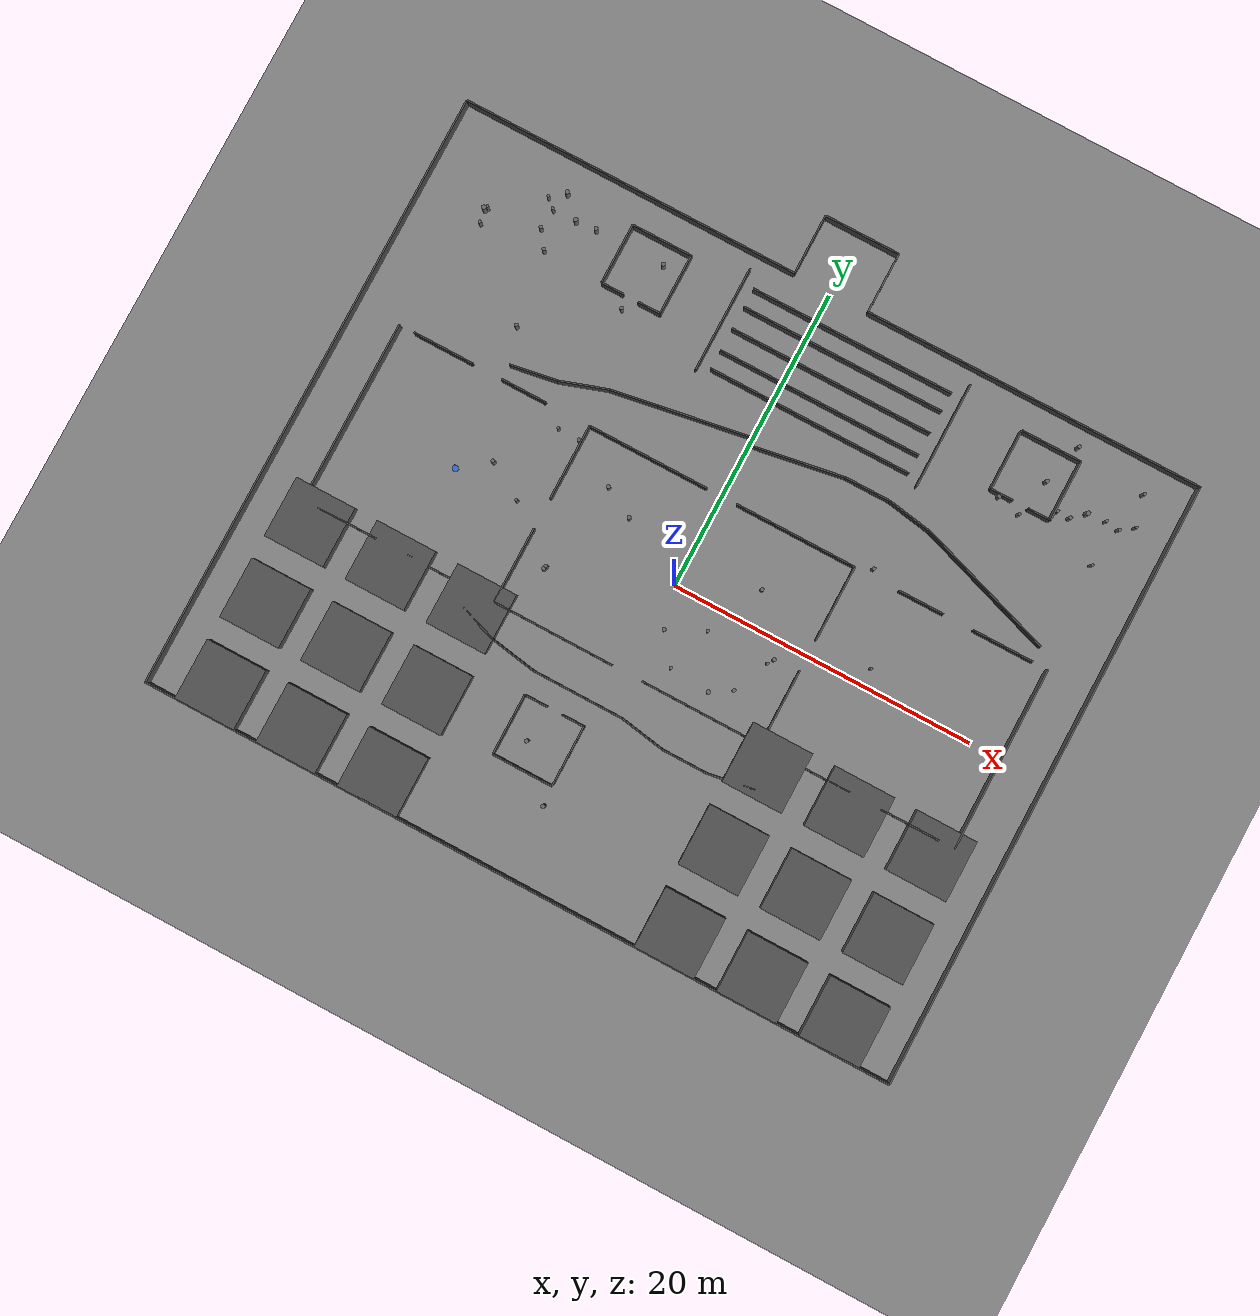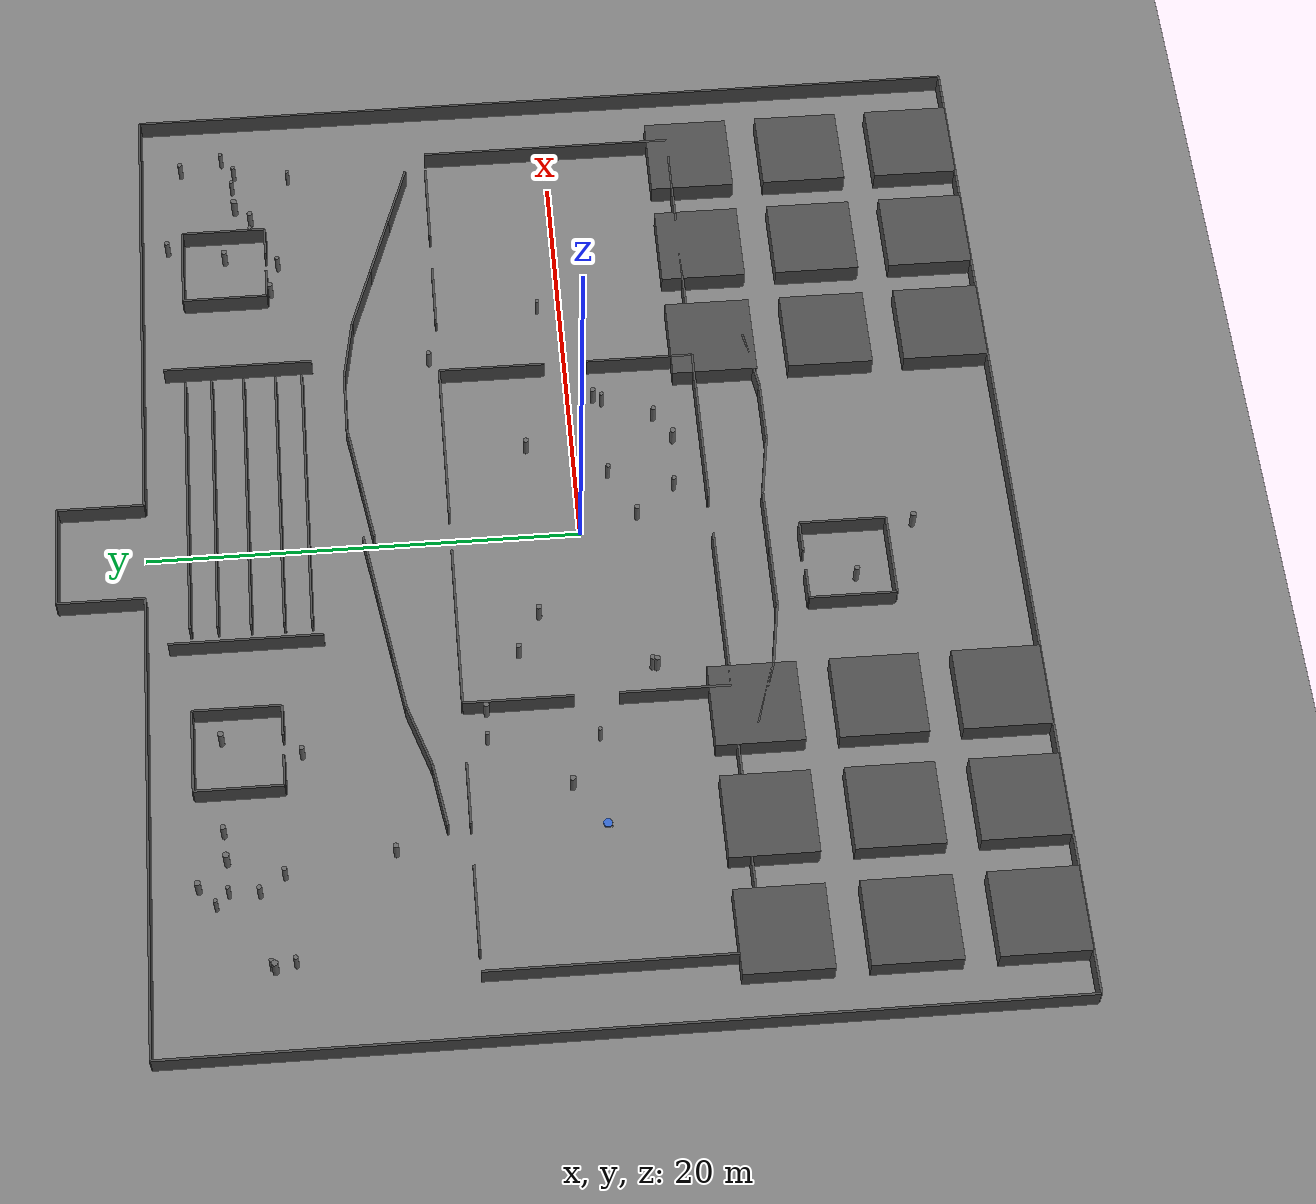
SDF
<?xml version="1.0" ?>
<sdf version="1.9">
  <world name="maze_large">
    <physics name="default" type="ignored">
      <max_step_size>0.001</max_step_size>
      <real_time_factor>1.0</real_time_factor>
    </physics>

    <plugin
      filename="gz-sim-physics-system"
      name="gz::sim::systems::Physics">
    </plugin>
    <plugin
      filename="gz-sim-sensors-system"
      name="gz::sim::systems::Sensors">
      <render_engine>ogre2</render_engine>
    </plugin>
    <plugin
      filename="gz-sim-scene-broadcaster-system"
      name="gz::sim::systems::SceneBroadcaster">
    </plugin>
    <plugin
      filename="gz-sim-user-commands-system"
      name="gz::sim::systems::UserCommands">
    </plugin>

    <scene>
      <ambient>0.4 0.4 0.4 1</ambient>
      <background>0.7 0.7 0.7 1</background>
      <shadows>false</shadows>
    </scene>

    <light name="sun" type="directional">
      <pose>0 0 20 0 0 0</pose>
      <diffuse>0.7 0.7 0.7 1</diffuse>
      <specular>0.2 0.2 0.2 1</specular>
    </light>

    <!-- Ground plane -->
    <model name="ground">
      <static>true</static>
      <link name="link">
        <collision name="collision">
          <geometry>
            <plane>
              <normal>0 0 1</normal>
              <size>75 60</size>
            </plane>
          </geometry>
        </collision>
        <visual name="visual">
          <geometry>
            <plane>
              <normal>0 0 1</normal>
              <size>75 60</size>
            </plane>
          </geometry>
          <material>
            <ambient>0.5 0.5 0.5 1</ambient>
            <diffuse>0.5 0.5 0.5 1</diffuse>
          </material>
        </visual>
      </link>
    </model>

    <!--  STRUCTURES                                                       -->

    <model name="border_top_l">
      <static>true</static>
      <pose>-13.75 20.0 0.5 0 0 0.0</pose>
      <link name="wall">
        <collision name="collision">
          <geometry><box><size>22.5 0.1 1.0</size></box></geometry>
        </collision>
        <visual name="visual">
          <geometry><box><size>22.5 0.1 1.0</size></box></geometry>
          <material><ambient>0.3 0.3 0.3 1</ambient><diffuse>0.3 0.3 0.3 1</diffuse></material>
        </visual>
      </link>
    </model>

    <model name="border_top_r">
      <static>true</static>
      <pose>13.75 20.0 0.5 0 0 0.0</pose>
      <link name="wall">
        <collision name="collision">
          <geometry><box><size>22.5 0.1 1.0</size></box></geometry>
        </collision>
        <visual name="visual">
          <geometry><box><size>22.5 0.1 1.0</size></box></geometry>
          <material><ambient>0.3 0.3 0.3 1</ambient><diffuse>0.3 0.3 0.3 1</diffuse></material>
        </visual>
      </link>
    </model>

    <model name="border_bottom">
      <static>true</static>
      <pose>0.0 -20.0 0.5 0 0 0.0</pose>
      <link name="wall">
        <collision name="collision">
          <geometry><box><size>50.0 0.1 1.0</size></box></geometry>
        </collision>
        <visual name="visual">
          <geometry><box><size>50.0 0.1 1.0</size></box></geometry>
          <material><ambient>0.3 0.3 0.3 1</ambient><diffuse>0.3 0.3 0.3 1</diffuse></material>
        </visual>
      </link>
    </model>

    <model name="border_left">
      <static>true</static>
      <pose>-25.0 0.0 0.5 0 0 0.0</pose>
      <link name="wall">
        <collision name="collision">
          <geometry><box><size>0.1 40.0 1.0</size></box></geometry>
        </collision>
        <visual name="visual">
          <geometry><box><size>0.1 40.0 1.0</size></box></geometry>
          <material><ambient>0.3 0.3 0.3 1</ambient><diffuse>0.3 0.3 0.3 1</diffuse></material>
        </visual>
      </link>
    </model>

    <model name="border_right">
      <static>true</static>
      <pose>25.0 0.0 0.5 0 0 0.0</pose>
      <link name="wall">
        <collision name="collision">
          <geometry><box><size>0.1 40.0 1.0</size></box></geometry>
        </collision>
        <visual name="visual">
          <geometry><box><size>0.1 40.0 1.0</size></box></geometry>
          <material><ambient>0.3 0.3 0.3 1</ambient><diffuse>0.3 0.3 0.3 1</diffuse></material>
        </visual>
      </link>
    </model>

    <model name="alcove_left">
      <static>true</static>
      <pose>-2.5 22.0 0.5 0 0 0.0</pose>
      <link name="wall">
        <collision name="collision">
          <geometry><box><size>0.1 4.0 1.0</size></box></geometry>
        </collision>
        <visual name="visual">
          <geometry><box><size>0.1 4.0 1.0</size></box></geometry>
          <material><ambient>0.3 0.3 0.3 1</ambient><diffuse>0.3 0.3 0.3 1</diffuse></material>
        </visual>
      </link>
    </model>

    <model name="alcove_right">
      <static>true</static>
      <pose>2.5 22.0 0.5 0 0 0.0</pose>
      <link name="wall">
        <collision name="collision">
          <geometry><box><size>0.1 4.0 1.0</size></box></geometry>
        </collision>
        <visual name="visual">
          <geometry><box><size>0.1 4.0 1.0</size></box></geometry>
          <material><ambient>0.3 0.3 0.3 1</ambient><diffuse>0.3 0.3 0.3 1</diffuse></material>
        </visual>
      </link>
    </model>

    <model name="alcove_back">
      <static>true</static>
      <pose>0.0 24.0 0.5 0 0 0.0</pose>
      <link name="wall">
        <collision name="collision">
          <geometry><box><size>5.0 0.1 1.0</size></box></geometry>
        </collision>
        <visual name="visual">
          <geometry><box><size>5.0 0.1 1.0</size></box></geometry>
          <material><ambient>0.3 0.3 0.3 1</ambient><diffuse>0.3 0.3 0.3 1</diffuse></material>
        </visual>
      </link>
    </model>

    <model name="plaza_top_l">
      <static>true</static>
      <pose>-5.0 6.0 0.5 0 0 0.0</pose>
      <link name="wall">
        <collision name="collision">
          <geometry><box><size>8.0 0.1 1.0</size></box></geometry>
        </collision>
        <visual name="visual">
          <geometry><box><size>8.0 0.1 1.0</size></box></geometry>
          <material><ambient>0.3 0.3 0.3 1</ambient><diffuse>0.3 0.3 0.3 1</diffuse></material>
        </visual>
      </link>
    </model>

    <model name="plaza_top_r">
      <static>true</static>
      <pose>5.0 6.0 0.5 0 0 0.0</pose>
      <link name="wall">
        <collision name="collision">
          <geometry><box><size>8.0 0.1 1.0</size></box></geometry>
        </collision>
        <visual name="visual">
          <geometry><box><size>8.0 0.1 1.0</size></box></geometry>
          <material><ambient>0.3 0.3 0.3 1</ambient><diffuse>0.3 0.3 0.3 1</diffuse></material>
        </visual>
      </link>
    </model>

    <model name="plaza_bot_l">
      <static>true</static>
      <pose>-5.0 -6.0 0.5 0 0 0.0</pose>
      <link name="wall">
        <collision name="collision">
          <geometry><box><size>8.0 0.1 1.0</size></box></geometry>
        </collision>
        <visual name="visual">
          <geometry><box><size>8.0 0.1 1.0</size></box></geometry>
          <material><ambient>0.3 0.3 0.3 1</ambient><diffuse>0.3 0.3 0.3 1</diffuse></material>
        </visual>
      </link>
    </model>

    <model name="plaza_bot_r">
      <static>true</static>
      <pose>5.0 -6.0 0.5 0 0 0.0</pose>
      <link name="wall">
        <collision name="collision">
          <geometry><box><size>8.0 0.1 1.0</size></box></geometry>
        </collision>
        <visual name="visual">
          <geometry><box><size>8.0 0.1 1.0</size></box></geometry>
          <material><ambient>0.3 0.3 0.3 1</ambient><diffuse>0.3 0.3 0.3 1</diffuse></material>
        </visual>
      </link>
    </model>

    <model name="plaza_left_t">
      <static>true</static>
      <pose>-9.0 3.5 0.5 0 0 0.0</pose>
      <link name="wall">
        <collision name="collision">
          <geometry><box><size>0.1 5.0 1.0</size></box></geometry>
        </collision>
        <visual name="visual">
          <geometry><box><size>0.1 5.0 1.0</size></box></geometry>
          <material><ambient>0.3 0.3 0.3 1</ambient><diffuse>0.3 0.3 0.3 1</diffuse></material>
        </visual>
      </link>
    </model>

    <model name="plaza_left_b">
      <static>true</static>
      <pose>-9.0 -3.5 0.5 0 0 0.0</pose>
      <link name="wall">
        <collision name="collision">
          <geometry><box><size>0.1 5.0 1.0</size></box></geometry>
        </collision>
        <visual name="visual">
          <geometry><box><size>0.1 5.0 1.0</size></box></geometry>
          <material><ambient>0.3 0.3 0.3 1</ambient><diffuse>0.3 0.3 0.3 1</diffuse></material>
        </visual>
      </link>
    </model>

    <model name="plaza_right_t">
      <static>true</static>
      <pose>9.0 3.5 0.5 0 0 0.0</pose>
      <link name="wall">
        <collision name="collision">
          <geometry><box><size>0.1 5.0 1.0</size></box></geometry>
        </collision>
        <visual name="visual">
          <geometry><box><size>0.1 5.0 1.0</size></box></geometry>
          <material><ambient>0.3 0.3 0.3 1</ambient><diffuse>0.3 0.3 0.3 1</diffuse></material>
        </visual>
      </link>
    </model>

    <model name="plaza_right_b">
      <static>true</static>
      <pose>9.0 -3.5 0.5 0 0 0.0</pose>
      <link name="wall">
        <collision name="collision">
          <geometry><box><size>0.1 5.0 1.0</size></box></geometry>
        </collision>
        <visual name="visual">
          <geometry><box><size>0.1 5.0 1.0</size></box></geometry>
          <material><ambient>0.3 0.3 0.3 1</ambient><diffuse>0.3 0.3 0.3 1</diffuse></material>
        </visual>
      </link>
    </model>

    <model name="plaza_p_0">
      <static>true</static>
      <pose>2.15 -4.5 0.5 0 0 0</pose>
      <link name="p">
        <collision name="c">
          <geometry><cylinder><radius>0.105</radius><length>1.0</length></cylinder></geometry>
        </collision>
        <visual name="v">
          <geometry><cylinder><radius>0.105</radius><length>1.0</length></cylinder></geometry>
          <material><ambient>0.4 0.4 0.4 1</ambient><diffuse>0.4 0.4 0.4 1</diffuse></material>
        </visual>
      </link>
    </model>

    <model name="plaza_p_1">
      <static>true</static>
      <pose>-4.3 2.25 0.5 0 0 0</pose>
      <link name="p">
        <collision name="c">
          <geometry><cylinder><radius>0.13</radius><length>1.0</length></cylinder></geometry>
        </collision>
        <visual name="v">
          <geometry><cylinder><radius>0.13</radius><length>1.0</length></cylinder></geometry>
          <material><ambient>0.4 0.4 0.4 1</ambient><diffuse>0.4 0.4 0.4 1</diffuse></material>
        </visual>
      </link>
    </model>

    <model name="plaza_p_2">
      <static>true</static>
      <pose>6.1 -3.9 0.5 0 0 0</pose>
      <link name="p">
        <collision name="c">
          <geometry><cylinder><radius>0.115</radius><length>1.0</length></cylinder></geometry>
        </collision>
        <visual name="v">
          <geometry><cylinder><radius>0.115</radius><length>1.0</length></cylinder></geometry>
          <material><ambient>0.4 0.4 0.4 1</ambient><diffuse>0.4 0.4 0.4 1</diffuse></material>
        </visual>
      </link>
    </model>

    <model name="plaza_p_3">
      <static>true</static>
      <pose>-7.3 -2.65 0.5 0 0 0</pose>
      <link name="p">
        <collision name="c">
          <geometry><cylinder><radius>0.12</radius><length>1.0</length></cylinder></geometry>
        </collision>
        <visual name="v">
          <geometry><cylinder><radius>0.12</radius><length>1.0</length></cylinder></geometry>
          <material><ambient>0.4 0.4 0.4 1</ambient><diffuse>0.4 0.4 0.4 1</diffuse></material>
        </visual>
      </link>
    </model>

    <model name="plaza_p_4">
      <static>true</static>
      <pose>-7.35 -2.85 0.5 0 0 0</pose>
      <link name="p">
        <collision name="c">
          <geometry><cylinder><radius>0.1275</radius><length>1.0</length></cylinder></geometry>
        </collision>
        <visual name="v">
          <geometry><cylinder><radius>0.1275</radius><length>1.0</length></cylinder></geometry>
          <material><ambient>0.4 0.4 0.4 1</ambient><diffuse>0.4 0.4 0.4 1</diffuse></material>
        </visual>
      </link>
    </model>

    <model name="plaza_p_5">
      <static>true</static>
      <pose>0.7 -2.65 0.5 0 0 0</pose>
      <link name="p">
        <collision name="c">
          <geometry><cylinder><radius>0.125</radius><length>1.0</length></cylinder></geometry>
        </collision>
        <visual name="v">
          <geometry><cylinder><radius>0.125</radius><length>1.0</length></cylinder></geometry>
          <material><ambient>0.4 0.4 0.4 1</ambient><diffuse>0.4 0.4 0.4 1</diffuse></material>
        </visual>
      </link>
    </model>

    <model name="plaza_p_6">
      <static>true</static>
      <pose>4.8 -4.7 0.5 0 0 0</pose>
      <link name="p">
        <collision name="c">
          <geometry><cylinder><radius>0.1375</radius><length>1.0</length></cylinder></geometry>
        </collision>
        <visual name="v">
          <geometry><cylinder><radius>0.1375</radius><length>1.0</length></cylinder></geometry>
          <material><ambient>0.4 0.4 0.4 1</ambient><diffuse>0.4 0.4 0.4 1</diffuse></material>
        </visual>
      </link>
    </model>

    <model name="plaza_p_7">
      <static>true</static>
      <pose>3.05 -1.5 0.5 0 0 0</pose>
      <link name="p">
        <collision name="c">
          <geometry><cylinder><radius>0.0975</radius><length>1.0</length></cylinder></geometry>
        </collision>
        <visual name="v">
          <geometry><cylinder><radius>0.0975</radius><length>1.0</length></cylinder></geometry>
          <material><ambient>0.4 0.4 0.4 1</ambient><diffuse>0.4 0.4 0.4 1</diffuse></material>
        </visual>
      </link>
    </model>

    <model name="plaza_p_8">
      <static>true</static>
      <pose>7.1 -1.55 0.5 0 0 0</pose>
      <link name="p">
        <collision name="c">
          <geometry><cylinder><radius>0.0925</radius><length>1.0</length></cylinder></geometry>
        </collision>
        <visual name="v">
          <geometry><cylinder><radius>0.0925</radius><length>1.0</length></cylinder></geometry>
          <material><ambient>0.4 0.4 0.4 1</ambient><diffuse>0.4 0.4 0.4 1</diffuse></material>
        </visual>
      </link>
    </model>

    <model name="plaza_p_9">
      <static>true</static>
      <pose>-6.25 3.3 0.5 0 0 0</pose>
      <link name="p">
        <collision name="c">
          <geometry><cylinder><radius>0.125</radius><length>1.0</length></cylinder></geometry>
        </collision>
        <visual name="v">
          <geometry><cylinder><radius>0.125</radius><length>1.0</length></cylinder></geometry>
          <material><ambient>0.4 0.4 0.4 1</ambient><diffuse>0.4 0.4 0.4 1</diffuse></material>
        </visual>
      </link>
    </model>

    <model name="plaza_p_10">
      <static>true</static>
      <pose>4.75 2.2 0.5 0 0 0</pose>
      <link name="p">
        <collision name="c">
          <geometry><cylinder><radius>0.12</radius><length>1.0</length></cylinder></geometry>
        </collision>
        <visual name="v">
          <geometry><cylinder><radius>0.12</radius><length>1.0</length></cylinder></geometry>
          <material><ambient>0.4 0.4 0.4 1</ambient><diffuse>0.4 0.4 0.4 1</diffuse></material>
        </visual>
      </link>
    </model>

    <model name="plaza_p_11">
      <static>true</static>
      <pose>7.35 -1.15 0.5 0 0 0</pose>
      <link name="p">
        <collision name="c">
          <geometry><cylinder><radius>0.1225</radius><length>1.0</length></cylinder></geometry>
        </collision>
        <visual name="v">
          <geometry><cylinder><radius>0.1225</radius><length>1.0</length></cylinder></geometry>
          <material><ambient>0.4 0.4 0.4 1</ambient><diffuse>0.4 0.4 0.4 1</diffuse></material>
        </visual>
      </link>
    </model>

    <model name="corr_l_out">
      <static>true</static>
      <pose>-22.0 0.0 0.5 0 0 0.0</pose>
      <link name="wall">
        <collision name="collision">
          <geometry><box><size>0.1 12.0 1.0</size></box></geometry>
        </collision>
        <visual name="visual">
          <geometry><box><size>0.1 12.0 1.0</size></box></geometry>
          <material><ambient>0.3 0.3 0.3 1</ambient><diffuse>0.3 0.3 0.3 1</diffuse></material>
        </visual>
      </link>
    </model>

    <model name="corr_l_top_l">
      <static>true</static>
      <pose>-19.0 6.0 0.5 0 0 0.0</pose>
      <link name="wall">
        <collision name="collision">
          <geometry><box><size>4.0 0.1 1.0</size></box></geometry>
        </collision>
        <visual name="visual">
          <geometry><box><size>4.0 0.1 1.0</size></box></geometry>
          <material><ambient>0.3 0.3 0.3 1</ambient><diffuse>0.3 0.3 0.3 1</diffuse></material>
        </visual>
      </link>
    </model>

    <model name="corr_l_top_r">
      <static>true</static>
      <pose>-13.5 6.0 0.5 0 0 0.0</pose>
      <link name="wall">
        <collision name="collision">
          <geometry><box><size>3.0 0.1 1.0</size></box></geometry>
        </collision>
        <visual name="visual">
          <geometry><box><size>3.0 0.1 1.0</size></box></geometry>
          <material><ambient>0.3 0.3 0.3 1</ambient><diffuse>0.3 0.3 0.3 1</diffuse></material>
        </visual>
      </link>
    </model>

    <model name="corr_l_bot_l">
      <static>true</static>
      <pose>-19.0 -6.0 0.5 0 0 0.0</pose>
      <link name="wall">
        <collision name="collision">
          <geometry><box><size>4.0 0.1 1.0</size></box></geometry>
        </collision>
        <visual name="visual">
          <geometry><box><size>4.0 0.1 1.0</size></box></geometry>
          <material><ambient>0.3 0.3 0.3 1</ambient><diffuse>0.3 0.3 0.3 1</diffuse></material>
        </visual>
      </link>
    </model>

    <model name="corr_l_bot_r">
      <static>true</static>
      <pose>-13.5 -6.0 0.5 0 0 0.0</pose>
      <link name="wall">
        <collision name="collision">
          <geometry><box><size>3.0 0.1 1.0</size></box></geometry>
        </collision>
        <visual name="visual">
          <geometry><box><size>3.0 0.1 1.0</size></box></geometry>
          <material><ambient>0.3 0.3 0.3 1</ambient><diffuse>0.3 0.3 0.3 1</diffuse></material>
        </visual>
      </link>
    </model>

    <model name="corr_r_out">
      <static>true</static>
      <pose>22.0 0.0 0.5 0 0 0.0</pose>
      <link name="wall">
        <collision name="collision">
          <geometry><box><size>0.1 12.0 1.0</size></box></geometry>
        </collision>
        <visual name="visual">
          <geometry><box><size>0.1 12.0 1.0</size></box></geometry>
          <material><ambient>0.3 0.3 0.3 1</ambient><diffuse>0.3 0.3 0.3 1</diffuse></material>
        </visual>
      </link>
    </model>

    <model name="corr_r_top_l">
      <static>true</static>
      <pose>13.5 6.0 0.5 0 0 0.0</pose>
      <link name="wall">
        <collision name="collision">
          <geometry><box><size>3.0 0.1 1.0</size></box></geometry>
        </collision>
        <visual name="visual">
          <geometry><box><size>3.0 0.1 1.0</size></box></geometry>
          <material><ambient>0.3 0.3 0.3 1</ambient><diffuse>0.3 0.3 0.3 1</diffuse></material>
        </visual>
      </link>
    </model>

    <model name="corr_r_top_r">
      <static>true</static>
      <pose>19.0 6.0 0.5 0 0 0.0</pose>
      <link name="wall">
        <collision name="collision">
          <geometry><box><size>4.0 0.1 1.0</size></box></geometry>
        </collision>
        <visual name="visual">
          <geometry><box><size>4.0 0.1 1.0</size></box></geometry>
          <material><ambient>0.3 0.3 0.3 1</ambient><diffuse>0.3 0.3 0.3 1</diffuse></material>
        </visual>
      </link>
    </model>

    <model name="corr_r_bot_l">
      <static>true</static>
      <pose>13.5 -6.0 0.5 0 0 0.0</pose>
      <link name="wall">
        <collision name="collision">
          <geometry><box><size>3.0 0.1 1.0</size></box></geometry>
        </collision>
        <visual name="visual">
          <geometry><box><size>3.0 0.1 1.0</size></box></geometry>
          <material><ambient>0.3 0.3 0.3 1</ambient><diffuse>0.3 0.3 0.3 1</diffuse></material>
        </visual>
      </link>
    </model>

    <model name="corr_r_bot_r">
      <static>true</static>
      <pose>19.0 -6.0 0.5 0 0 0.0</pose>
      <link name="wall">
        <collision name="collision">
          <geometry><box><size>4.0 0.1 1.0</size></box></geometry>
        </collision>
        <visual name="visual">
          <geometry><box><size>4.0 0.1 1.0</size></box></geometry>
          <material><ambient>0.3 0.3 0.3 1</ambient><diffuse>0.3 0.3 0.3 1</diffuse></material>
        </visual>
      </link>
    </model>

    <model name="pf_left_0">
      <static>true</static>
      <pose>-15.7 16.65 0.5 0 0 0</pose>
      <link name="p">
        <collision name="c">
          <geometry><cylinder><radius>0.1425</radius><length>1.0</length></cylinder></geometry>
        </collision>
        <visual name="v">
          <geometry><cylinder><radius>0.1425</radius><length>1.0</length></cylinder></geometry>
          <material><ambient>0.4 0.4 0.4 1</ambient><diffuse>0.4 0.4 0.4 1</diffuse></material>
        </visual>
      </link>
    </model>

    <model name="pf_left_1">
      <static>true</static>
      <pose>-17.85 17.15 0.5 0 0 0</pose>
      <link name="p">
        <collision name="c">
          <geometry><cylinder><radius>0.09</radius><length>1.0</length></cylinder></geometry>
        </collision>
        <visual name="v">
          <geometry><cylinder><radius>0.09</radius><length>1.0</length></cylinder></geometry>
          <material><ambient>0.4 0.4 0.4 1</ambient><diffuse>0.4 0.4 0.4 1</diffuse></material>
        </visual>
      </link>
    </model>

    <model name="pf_left_2">
      <static>true</static>
      <pose>-20.8 14.85 0.5 0 0 0</pose>
      <link name="p">
        <collision name="c">
          <geometry><cylinder><radius>0.0925</radius><length>1.0</length></cylinder></geometry>
        </collision>
        <visual name="v">
          <geometry><cylinder><radius>0.0925</radius><length>1.0</length></cylinder></geometry>
          <material><ambient>0.4 0.4 0.4 1</ambient><diffuse>0.4 0.4 0.4 1</diffuse></material>
        </visual>
      </link>
    </model>

    <model name="pf_left_3">
      <static>true</static>
      <pose>-20.75 13.8 0.5 0 0 0</pose>
      <link name="p">
        <collision name="c">
          <geometry><cylinder><radius>0.105</radius><length>1.0</length></cylinder></geometry>
        </collision>
        <visual name="v">
          <geometry><cylinder><radius>0.105</radius><length>1.0</length></cylinder></geometry>
          <material><ambient>0.4 0.4 0.4 1</ambient><diffuse>0.4 0.4 0.4 1</diffuse></material>
        </visual>
      </link>
    </model>

    <model name="pf_left_4">
      <static>true</static>
      <pose>-17.35 15.25 0.5 0 0 0</pose>
      <link name="p">
        <collision name="c">
          <geometry><cylinder><radius>0.11</radius><length>1.0</length></cylinder></geometry>
        </collision>
        <visual name="v">
          <geometry><cylinder><radius>0.11</radius><length>1.0</length></cylinder></geometry>
          <material><ambient>0.4 0.4 0.4 1</ambient><diffuse>0.4 0.4 0.4 1</diffuse></material>
        </visual>
      </link>
    </model>

    <model name="pf_left_5">
      <static>true</static>
      <pose>-20.95 14.7 0.5 0 0 0</pose>
      <link name="p">
        <collision name="c">
          <geometry><cylinder><radius>0.145</radius><length>1.0</length></cylinder></geometry>
        </collision>
        <visual name="v">
          <geometry><cylinder><radius>0.145</radius><length>1.0</length></cylinder></geometry>
          <material><ambient>0.4 0.4 0.4 1</ambient><diffuse>0.4 0.4 0.4 1</diffuse></material>
        </visual>
      </link>
    </model>

    <model name="pf_left_6">
      <static>true</static>
      <pose>-17.25 16.6 0.5 0 0 0</pose>
      <link name="p">
        <collision name="c">
          <geometry><cylinder><radius>0.0975</radius><length>1.0</length></cylinder></geometry>
        </collision>
        <visual name="v">
          <geometry><cylinder><radius>0.0975</radius><length>1.0</length></cylinder></geometry>
          <material><ambient>0.4 0.4 0.4 1</ambient><diffuse>0.4 0.4 0.4 1</diffuse></material>
        </visual>
      </link>
    </model>

    <model name="pf_left_7">
      <static>true</static>
      <pose>-16.55 14.15 0.5 0 0 0</pose>
      <link name="p">
        <collision name="c">
          <geometry><cylinder><radius>0.11</radius><length>1.0</length></cylinder></geometry>
        </collision>
        <visual name="v">
          <geometry><cylinder><radius>0.11</radius><length>1.0</length></cylinder></geometry>
          <material><ambient>0.4 0.4 0.4 1</ambient><diffuse>0.4 0.4 0.4 1</diffuse></material>
        </visual>
      </link>
    </model>

    <model name="pf_left_8">
      <static>true</static>
      <pose>-14.35 16.75 0.5 0 0 0</pose>
      <link name="p">
        <collision name="c">
          <geometry><cylinder><radius>0.1225</radius><length>1.0</length></cylinder></geometry>
        </collision>
        <visual name="v">
          <geometry><cylinder><radius>0.1225</radius><length>1.0</length></cylinder></geometry>
          <material><ambient>0.4 0.4 0.4 1</ambient><diffuse>0.4 0.4 0.4 1</diffuse></material>
        </visual>
      </link>
    </model>

    <model name="pf_left_9">
      <static>true</static>
      <pose>-16.95 17.9 0.5 0 0 0</pose>
      <link name="p">
        <collision name="c">
          <geometry><cylinder><radius>0.135</radius><length>1.0</length></cylinder></geometry>
        </collision>
        <visual name="v">
          <geometry><cylinder><radius>0.135</radius><length>1.0</length></cylinder></geometry>
          <material><ambient>0.4 0.4 0.4 1</ambient><diffuse>0.4 0.4 0.4 1</diffuse></material>
        </visual>
      </link>
    </model>

    <model name="pf_right_0">
      <static>true</static>
      <pose>16.2 13.45 0.5 0 0 0</pose>
      <link name="p">
        <collision name="c">
          <geometry><cylinder><radius>0.1075</radius><length>1.0</length></cylinder></geometry>
        </collision>
        <visual name="v">
          <geometry><cylinder><radius>0.1075</radius><length>1.0</length></cylinder></geometry>
          <material><ambient>0.4 0.4 0.4 1</ambient><diffuse>0.4 0.4 0.4 1</diffuse></material>
        </visual>
      </link>
    </model>

    <model name="pf_right_1">
      <static>true</static>
      <pose>22.25 18.05 0.5 0 0 0</pose>
      <link name="p">
        <collision name="c">
          <geometry><cylinder><radius>0.1075</radius><length>1.0</length></cylinder></geometry>
        </collision>
        <visual name="v">
          <geometry><cylinder><radius>0.1075</radius><length>1.0</length></cylinder></geometry>
          <material><ambient>0.4 0.4 0.4 1</ambient><diffuse>0.4 0.4 0.4 1</diffuse></material>
        </visual>
      </link>
    </model>

    <model name="pf_right_2">
      <static>true</static>
      <pose>19.8 15.45 0.5 0 0 0</pose>
      <link name="p">
        <collision name="c">
          <geometry><cylinder><radius>0.145</radius><length>1.0</length></cylinder></geometry>
        </collision>
        <visual name="v">
          <geometry><cylinder><radius>0.145</radius><length>1.0</length></cylinder></geometry>
          <material><ambient>0.4 0.4 0.4 1</ambient><diffuse>0.4 0.4 0.4 1</diffuse></material>
        </visual>
      </link>
    </model>

    <model name="pf_right_3">
      <static>true</static>
      <pose>18.15 14.7 0.5 0 0 0</pose>
      <link name="p">
        <collision name="c">
          <geometry><cylinder><radius>0.1025</radius><length>1.0</length></cylinder></geometry>
        </collision>
        <visual name="v">
          <geometry><cylinder><radius>0.1025</radius><length>1.0</length></cylinder></geometry>
          <material><ambient>0.4 0.4 0.4 1</ambient><diffuse>0.4 0.4 0.4 1</diffuse></material>
        </visual>
      </link>
    </model>

    <model name="pf_right_4">
      <static>true</static>
      <pose>19.0 14.7 0.5 0 0 0</pose>
      <link name="p">
        <collision name="c">
          <geometry><cylinder><radius>0.125</radius><length>1.0</length></cylinder></geometry>
        </collision>
        <visual name="v">
          <geometry><cylinder><radius>0.125</radius><length>1.0</length></cylinder></geometry>
          <material><ambient>0.4 0.4 0.4 1</ambient><diffuse>0.4 0.4 0.4 1</diffuse></material>
        </visual>
      </link>
    </model>

    <model name="pf_right_5">
      <static>true</static>
      <pose>21.9 15.45 0.5 0 0 0</pose>
      <link name="p">
        <collision name="c">
          <geometry><cylinder><radius>0.1</radius><length>1.0</length></cylinder></geometry>
        </collision>
        <visual name="v">
          <geometry><cylinder><radius>0.1</radius><length>1.0</length></cylinder></geometry>
          <material><ambient>0.4 0.4 0.4 1</ambient><diffuse>0.4 0.4 0.4 1</diffuse></material>
        </visual>
      </link>
    </model>

    <model name="pf_right_6">
      <static>true</static>
      <pose>22.75 16.05 0.5 0 0 0</pose>
      <link name="p">
        <collision name="c">
          <geometry><cylinder><radius>0.0925</radius><length>1.0</length></cylinder></geometry>
        </collision>
        <visual name="v">
          <geometry><cylinder><radius>0.0925</radius><length>1.0</length></cylinder></geometry>
          <material><ambient>0.4 0.4 0.4 1</ambient><diffuse>0.4 0.4 0.4 1</diffuse></material>
        </visual>
      </link>
    </model>

    <model name="pf_right_7">
      <static>true</static>
      <pose>14.65 13.85 0.5 0 0 0</pose>
      <link name="p">
        <collision name="c">
          <geometry><cylinder><radius>0.1275</radius><length>1.0</length></cylinder></geometry>
        </collision>
        <visual name="v">
          <geometry><cylinder><radius>0.1275</radius><length>1.0</length></cylinder></geometry>
          <material><ambient>0.4 0.4 0.4 1</ambient><diffuse>0.4 0.4 0.4 1</diffuse></material>
        </visual>
      </link>
    </model>

    <model name="pf_right_8">
      <static>true</static>
      <pose>21.0 15.55 0.5 0 0 0</pose>
      <link name="p">
        <collision name="c">
          <geometry><cylinder><radius>0.0925</radius><length>1.0</length></cylinder></geometry>
        </collision>
        <visual name="v">
          <geometry><cylinder><radius>0.0925</radius><length>1.0</length></cylinder></geometry>
          <material><ambient>0.4 0.4 0.4 1</ambient><diffuse>0.4 0.4 0.4 1</diffuse></material>
        </visual>
      </link>
    </model>

    <model name="pf_right_9">
      <static>true</static>
      <pose>17.5 18.75 0.5 0 0 0</pose>
      <link name="p">
        <collision name="c">
          <geometry><cylinder><radius>0.12</radius><length>1.0</length></cylinder></geometry>
        </collision>
        <visual name="v">
          <geometry><cylinder><radius>0.12</radius><length>1.0</length></cylinder></geometry>
          <material><ambient>0.4 0.4 0.4 1</ambient><diffuse>0.4 0.4 0.4 1</diffuse></material>
        </visual>
      </link>
    </model>

    <model name="room_a_bot_l">
      <static>true</static>
      <pose>-11.75 14.0 0.5 0 0 0.0</pose>
      <link name="wall">
        <collision name="collision">
          <geometry><box><size>1.5 0.1 1.0</size></box></geometry>
        </collision>
        <visual name="visual">
          <geometry><box><size>1.5 0.1 1.0</size></box></geometry>
          <material><ambient>0.3 0.3 0.3 1</ambient><diffuse>0.3 0.3 0.3 1</diffuse></material>
        </visual>
      </link>
    </model>

    <model name="room_a_bot_r">
      <static>true</static>
      <pose>-9.25 14.0 0.5 0 0 0.0</pose>
      <link name="wall">
        <collision name="collision">
          <geometry><box><size>1.5 0.1 1.0</size></box></geometry>
        </collision>
        <visual name="visual">
          <geometry><box><size>1.5 0.1 1.0</size></box></geometry>
          <material><ambient>0.3 0.3 0.3 1</ambient><diffuse>0.3 0.3 0.3 1</diffuse></material>
        </visual>
      </link>
    </model>

    <model name="room_a_top">
      <static>true</static>
      <pose>-10.5 18.0 0.5 0 0 0.0</pose>
      <link name="wall">
        <collision name="collision">
          <geometry><box><size>4.0 0.1 1.0</size></box></geometry>
        </collision>
        <visual name="visual">
          <geometry><box><size>4.0 0.1 1.0</size></box></geometry>
          <material><ambient>0.3 0.3 0.3 1</ambient><diffuse>0.3 0.3 0.3 1</diffuse></material>
        </visual>
      </link>
    </model>

    <model name="room_a_left">
      <static>true</static>
      <pose>-12.5 16.0 0.5 0 0 0.0</pose>
      <link name="wall">
        <collision name="collision">
          <geometry><box><size>0.1 4.0 1.0</size></box></geometry>
        </collision>
        <visual name="visual">
          <geometry><box><size>0.1 4.0 1.0</size></box></geometry>
          <material><ambient>0.3 0.3 0.3 1</ambient><diffuse>0.3 0.3 0.3 1</diffuse></material>
        </visual>
      </link>
    </model>

    <model name="room_a_right">
      <static>true</static>
      <pose>-8.5 16.0 0.5 0 0 0.0</pose>
      <link name="wall">
        <collision name="collision">
          <geometry><box><size>0.1 4.0 1.0</size></box></geometry>
        </collision>
        <visual name="visual">
          <geometry><box><size>0.1 4.0 1.0</size></box></geometry>
          <material><ambient>0.3 0.3 0.3 1</ambient><diffuse>0.3 0.3 0.3 1</diffuse></material>
        </visual>
      </link>
    </model>

    <model name="room_a_pillar">
      <static>true</static>
      <pose>-9.75 16.75 0.5 0 0 0</pose>
      <link name="p">
        <collision name="c">
          <geometry><cylinder><radius>0.125</radius><length>1.0</length></cylinder></geometry>
        </collision>
        <visual name="v">
          <geometry><cylinder><radius>0.125</radius><length>1.0</length></cylinder></geometry>
          <material><ambient>0.4 0.4 0.4 1</ambient><diffuse>0.4 0.4 0.4 1</diffuse></material>
        </visual>
      </link>
    </model>

    <model name="room_b_bot_l">
      <static>true</static>
      <pose>14.75 14.0 0.5 0 0 0.0</pose>
      <link name="wall">
        <collision name="collision">
          <geometry><box><size>1.5 0.1 1.0</size></box></geometry>
        </collision>
        <visual name="visual">
          <geometry><box><size>1.5 0.1 1.0</size></box></geometry>
          <material><ambient>0.3 0.3 0.3 1</ambient><diffuse>0.3 0.3 0.3 1</diffuse></material>
        </visual>
      </link>
    </model>

    <model name="room_b_bot_r">
      <static>true</static>
      <pose>17.25 14.0 0.5 0 0 0.0</pose>
      <link name="wall">
        <collision name="collision">
          <geometry><box><size>1.5 0.1 1.0</size></box></geometry>
        </collision>
        <visual name="visual">
          <geometry><box><size>1.5 0.1 1.0</size></box></geometry>
          <material><ambient>0.3 0.3 0.3 1</ambient><diffuse>0.3 0.3 0.3 1</diffuse></material>
        </visual>
      </link>
    </model>

    <model name="room_b_top">
      <static>true</static>
      <pose>16.0 18.0 0.5 0 0 0.0</pose>
      <link name="wall">
        <collision name="collision">
          <geometry><box><size>4.0 0.1 1.0</size></box></geometry>
        </collision>
        <visual name="visual">
          <geometry><box><size>4.0 0.1 1.0</size></box></geometry>
          <material><ambient>0.3 0.3 0.3 1</ambient><diffuse>0.3 0.3 0.3 1</diffuse></material>
        </visual>
      </link>
    </model>

    <model name="room_b_left">
      <static>true</static>
      <pose>14.0 16.0 0.5 0 0 0.0</pose>
      <link name="wall">
        <collision name="collision">
          <geometry><box><size>0.1 4.0 1.0</size></box></geometry>
        </collision>
        <visual name="visual">
          <geometry><box><size>0.1 4.0 1.0</size></box></geometry>
          <material><ambient>0.3 0.3 0.3 1</ambient><diffuse>0.3 0.3 0.3 1</diffuse></material>
        </visual>
      </link>
    </model>

    <model name="room_b_right">
      <static>true</static>
      <pose>18.0 16.0 0.5 0 0 0.0</pose>
      <link name="wall">
        <collision name="collision">
          <geometry><box><size>0.1 4.0 1.0</size></box></geometry>
        </collision>
        <visual name="visual">
          <geometry><box><size>0.1 4.0 1.0</size></box></geometry>
          <material><ambient>0.3 0.3 0.3 1</ambient><diffuse>0.3 0.3 0.3 1</diffuse></material>
        </visual>
      </link>
    </model>

    <model name="room_b_pillar">
      <static>true</static>
      <pose>16.75 16.0 0.5 0 0 0</pose>
      <link name="p">
        <collision name="c">
          <geometry><cylinder><radius>0.125</radius><length>1.0</length></cylinder></geometry>
        </collision>
        <visual name="v">
          <geometry><cylinder><radius>0.125</radius><length>1.0</length></cylinder></geometry>
          <material><ambient>0.4 0.4 0.4 1</ambient><diffuse>0.4 0.4 0.4 1</diffuse></material>
        </visual>
      </link>
    </model>

    <model name="room_c_bot">
      <static>true</static>
      <pose>-2.75 -14.0 0.5 0 0 0.0</pose>
      <link name="wall">
        <collision name="collision">
          <geometry><box><size>4.0 0.1 1.0</size></box></geometry>
        </collision>
        <visual name="visual">
          <geometry><box><size>4.0 0.1 1.0</size></box></geometry>
          <material><ambient>0.3 0.3 0.3 1</ambient><diffuse>0.3 0.3 0.3 1</diffuse></material>
        </visual>
      </link>
    </model>

    <model name="room_c_top_l">
      <static>true</static>
      <pose>-4.0 -10.0 0.5 0 0 0.0</pose>
      <link name="wall">
        <collision name="collision">
          <geometry><box><size>1.5 0.1 1.0</size></box></geometry>
        </collision>
        <visual name="visual">
          <geometry><box><size>1.5 0.1 1.0</size></box></geometry>
          <material><ambient>0.3 0.3 0.3 1</ambient><diffuse>0.3 0.3 0.3 1</diffuse></material>
        </visual>
      </link>
    </model>

    <model name="room_c_top_r">
      <static>true</static>
      <pose>-1.5 -10.0 0.5 0 0 0.0</pose>
      <link name="wall">
        <collision name="collision">
          <geometry><box><size>1.5 0.1 1.0</size></box></geometry>
        </collision>
        <visual name="visual">
          <geometry><box><size>1.5 0.1 1.0</size></box></geometry>
          <material><ambient>0.3 0.3 0.3 1</ambient><diffuse>0.3 0.3 0.3 1</diffuse></material>
        </visual>
      </link>
    </model>

    <model name="room_c_left">
      <static>true</static>
      <pose>-4.75 -12.0 0.5 0 0 0.0</pose>
      <link name="wall">
        <collision name="collision">
          <geometry><box><size>0.1 4.0 1.0</size></box></geometry>
        </collision>
        <visual name="visual">
          <geometry><box><size>0.1 4.0 1.0</size></box></geometry>
          <material><ambient>0.3 0.3 0.3 1</ambient><diffuse>0.3 0.3 0.3 1</diffuse></material>
        </visual>
      </link>
    </model>

    <model name="room_c_right">
      <static>true</static>
      <pose>-0.75 -12.0 0.5 0 0 0.0</pose>
      <link name="wall">
        <collision name="collision">
          <geometry><box><size>0.1 4.0 1.0</size></box></geometry>
        </collision>
        <visual name="visual">
          <geometry><box><size>0.1 4.0 1.0</size></box></geometry>
          <material><ambient>0.3 0.3 0.3 1</ambient><diffuse>0.3 0.3 0.3 1</diffuse></material>
        </visual>
      </link>
    </model>

    <model name="room_c_pillar">
      <static>true</static>
      <pose>-3.35 -12.35 0.5 0 0 0</pose>
      <link name="p">
        <collision name="c">
          <geometry><cylinder><radius>0.125</radius><length>1.0</length></cylinder></geometry>
        </collision>
        <visual name="v">
          <geometry><cylinder><radius>0.125</radius><length>1.0</length></cylinder></geometry>
          <material><ambient>0.4 0.4 0.4 1</ambient><diffuse>0.4 0.4 0.4 1</diffuse></material>
        </visual>
      </link>
    </model>

    <model name="warehouse_left">
      <static>true</static>
      <pose>-5.0 15.5 0.5 0 0 0.0</pose>
      <link name="wall">
        <collision name="collision">
          <geometry><box><size>0.1 7.0 1.0</size></box></geometry>
        </collision>
        <visual name="visual">
          <geometry><box><size>0.1 7.0 1.0</size></box></geometry>
          <material><ambient>0.3 0.3 0.3 1</ambient><diffuse>0.3 0.3 0.3 1</diffuse></material>
        </visual>
      </link>
    </model>

    <model name="warehouse_right">
      <static>true</static>
      <pose>10.0 15.5 0.5 0 0 0.0</pose>
      <link name="wall">
        <collision name="collision">
          <geometry><box><size>0.1 7.0 1.0</size></box></geometry>
        </collision>
        <visual name="visual">
          <geometry><box><size>0.1 7.0 1.0</size></box></geometry>
          <material><ambient>0.3 0.3 0.3 1</ambient><diffuse>0.3 0.3 0.3 1</diffuse></material>
        </visual>
      </link>
    </model>

    <model name="shelf_0">
      <static>true</static>
      <pose>2.5 12.5 0.5 0 0 0.0</pose>
      <link name="wall">
        <collision name="collision">
          <geometry><box><size>13.5 0.1 1.0</size></box></geometry>
        </collision>
        <visual name="visual">
          <geometry><box><size>13.5 0.1 1.0</size></box></geometry>
          <material><ambient>0.3 0.3 0.3 1</ambient><diffuse>0.3 0.3 0.3 1</diffuse></material>
        </visual>
      </link>
    </model>

    <model name="shelf_1">
      <static>true</static>
      <pose>2.5 13.75 0.5 0 0 0.0</pose>
      <link name="wall">
        <collision name="collision">
          <geometry><box><size>13.5 0.1 1.0</size></box></geometry>
        </collision>
        <visual name="visual">
          <geometry><box><size>13.5 0.1 1.0</size></box></geometry>
          <material><ambient>0.3 0.3 0.3 1</ambient><diffuse>0.3 0.3 0.3 1</diffuse></material>
        </visual>
      </link>
    </model>

    <model name="shelf_2">
      <static>true</static>
      <pose>2.5 15.25 0.5 0 0 0.0</pose>
      <link name="wall">
        <collision name="collision">
          <geometry><box><size>13.5 0.1 1.0</size></box></geometry>
        </collision>
        <visual name="visual">
          <geometry><box><size>13.5 0.1 1.0</size></box></geometry>
          <material><ambient>0.3 0.3 0.3 1</ambient><diffuse>0.3 0.3 0.3 1</diffuse></material>
        </visual>
      </link>
    </model>

    <model name="shelf_3">
      <static>true</static>
      <pose>2.5 16.75 0.5 0 0 0.0</pose>
      <link name="wall">
        <collision name="collision">
          <geometry><box><size>13.5 0.1 1.0</size></box></geometry>
        </collision>
        <visual name="visual">
          <geometry><box><size>13.5 0.1 1.0</size></box></geometry>
          <material><ambient>0.3 0.3 0.3 1</ambient><diffuse>0.3 0.3 0.3 1</diffuse></material>
        </visual>
      </link>
    </model>

    <model name="shelf_4">
      <static>true</static>
      <pose>2.5 18.0 0.5 0 0 0.0</pose>
      <link name="wall">
        <collision name="collision">
          <geometry><box><size>13.5 0.1 1.0</size></box></geometry>
        </collision>
        <visual name="visual">
          <geometry><box><size>13.5 0.1 1.0</size></box></geometry>
          <material><ambient>0.3 0.3 0.3 1</ambient><diffuse>0.3 0.3 0.3 1</diffuse></material>
        </visual>
      </link>
    </model>

    <model name="grid_l_0_0">
      <static>true</static>
      <pose>-21.0 -18.0 0.5 0 0 0.0</pose>
      <link name="wall">
        <collision name="collision">
          <geometry><box><size>4.0 4.0 1.0</size></box></geometry>
        </collision>
        <visual name="visual">
          <geometry><box><size>4.0 4.0 1.0</size></box></geometry>
          <material><ambient>0.3 0.3 0.3 1</ambient><diffuse>0.3 0.3 0.3 1</diffuse></material>
        </visual>
      </link>
    </model>

    <model name="grid_l_0_1">
      <static>true</static>
      <pose>-15.5 -18.0 0.5 0 0 0.0</pose>
      <link name="wall">
        <collision name="collision">
          <geometry><box><size>4.0 4.0 1.0</size></box></geometry>
        </collision>
        <visual name="visual">
          <geometry><box><size>4.0 4.0 1.0</size></box></geometry>
          <material><ambient>0.3 0.3 0.3 1</ambient><diffuse>0.3 0.3 0.3 1</diffuse></material>
        </visual>
      </link>
    </model>

    <model name="grid_l_0_2">
      <static>true</static>
      <pose>-10.0 -18.0 0.5 0 0 0.0</pose>
      <link name="wall">
        <collision name="collision">
          <geometry><box><size>4.0 4.0 1.0</size></box></geometry>
        </collision>
        <visual name="visual">
          <geometry><box><size>4.0 4.0 1.0</size></box></geometry>
          <material><ambient>0.3 0.3 0.3 1</ambient><diffuse>0.3 0.3 0.3 1</diffuse></material>
        </visual>
      </link>
    </model>

    <model name="grid_l_1_0">
      <static>true</static>
      <pose>-21.0 -12.5 0.5 0 0 0.0</pose>
      <link name="wall">
        <collision name="collision">
          <geometry><box><size>4.0 4.0 1.0</size></box></geometry>
        </collision>
        <visual name="visual">
          <geometry><box><size>4.0 4.0 1.0</size></box></geometry>
          <material><ambient>0.3 0.3 0.3 1</ambient><diffuse>0.3 0.3 0.3 1</diffuse></material>
        </visual>
      </link>
    </model>

    <model name="grid_l_1_1">
      <static>true</static>
      <pose>-15.5 -12.5 0.5 0 0 0.0</pose>
      <link name="wall">
        <collision name="collision">
          <geometry><box><size>4.0 4.0 1.0</size></box></geometry>
        </collision>
        <visual name="visual">
          <geometry><box><size>4.0 4.0 1.0</size></box></geometry>
          <material><ambient>0.3 0.3 0.3 1</ambient><diffuse>0.3 0.3 0.3 1</diffuse></material>
        </visual>
      </link>
    </model>

    <model name="grid_l_1_2">
      <static>true</static>
      <pose>-10.0 -12.5 0.5 0 0 0.0</pose>
      <link name="wall">
        <collision name="collision">
          <geometry><box><size>4.0 4.0 1.0</size></box></geometry>
        </collision>
        <visual name="visual">
          <geometry><box><size>4.0 4.0 1.0</size></box></geometry>
          <material><ambient>0.3 0.3 0.3 1</ambient><diffuse>0.3 0.3 0.3 1</diffuse></material>
        </visual>
      </link>
    </model>

    <model name="grid_l_2_0">
      <static>true</static>
      <pose>-21.0 -7.0 0.5 0 0 0.0</pose>
      <link name="wall">
        <collision name="collision">
          <geometry><box><size>4.0 4.0 1.0</size></box></geometry>
        </collision>
        <visual name="visual">
          <geometry><box><size>4.0 4.0 1.0</size></box></geometry>
          <material><ambient>0.3 0.3 0.3 1</ambient><diffuse>0.3 0.3 0.3 1</diffuse></material>
        </visual>
      </link>
    </model>

    <model name="grid_l_2_1">
      <static>true</static>
      <pose>-15.5 -7.0 0.5 0 0 0.0</pose>
      <link name="wall">
        <collision name="collision">
          <geometry><box><size>4.0 4.0 1.0</size></box></geometry>
        </collision>
        <visual name="visual">
          <geometry><box><size>4.0 4.0 1.0</size></box></geometry>
          <material><ambient>0.3 0.3 0.3 1</ambient><diffuse>0.3 0.3 0.3 1</diffuse></material>
        </visual>
      </link>
    </model>

    <model name="grid_l_2_2">
      <static>true</static>
      <pose>-10.0 -7.0 0.5 0 0 0.0</pose>
      <link name="wall">
        <collision name="collision">
          <geometry><box><size>4.0 4.0 1.0</size></box></geometry>
        </collision>
        <visual name="visual">
          <geometry><box><size>4.0 4.0 1.0</size></box></geometry>
          <material><ambient>0.3 0.3 0.3 1</ambient><diffuse>0.3 0.3 0.3 1</diffuse></material>
        </visual>
      </link>
    </model>

    <model name="grid_r_0_0">
      <static>true</static>
      <pose>10.0 -18.0 0.5 0 0 0.0</pose>
      <link name="wall">
        <collision name="collision">
          <geometry><box><size>4.0 4.0 1.0</size></box></geometry>
        </collision>
        <visual name="visual">
          <geometry><box><size>4.0 4.0 1.0</size></box></geometry>
          <material><ambient>0.3 0.3 0.3 1</ambient><diffuse>0.3 0.3 0.3 1</diffuse></material>
        </visual>
      </link>
    </model>

    <model name="grid_r_0_1">
      <static>true</static>
      <pose>15.5 -18.0 0.5 0 0 0.0</pose>
      <link name="wall">
        <collision name="collision">
          <geometry><box><size>4.0 4.0 1.0</size></box></geometry>
        </collision>
        <visual name="visual">
          <geometry><box><size>4.0 4.0 1.0</size></box></geometry>
          <material><ambient>0.3 0.3 0.3 1</ambient><diffuse>0.3 0.3 0.3 1</diffuse></material>
        </visual>
      </link>
    </model>

    <model name="grid_r_0_2">
      <static>true</static>
      <pose>21.0 -18.0 0.5 0 0 0.0</pose>
      <link name="wall">
        <collision name="collision">
          <geometry><box><size>4.0 4.0 1.0</size></box></geometry>
        </collision>
        <visual name="visual">
          <geometry><box><size>4.0 4.0 1.0</size></box></geometry>
          <material><ambient>0.3 0.3 0.3 1</ambient><diffuse>0.3 0.3 0.3 1</diffuse></material>
        </visual>
      </link>
    </model>

    <model name="grid_r_1_0">
      <static>true</static>
      <pose>10.0 -12.5 0.5 0 0 0.0</pose>
      <link name="wall">
        <collision name="collision">
          <geometry><box><size>4.0 4.0 1.0</size></box></geometry>
        </collision>
        <visual name="visual">
          <geometry><box><size>4.0 4.0 1.0</size></box></geometry>
          <material><ambient>0.3 0.3 0.3 1</ambient><diffuse>0.3 0.3 0.3 1</diffuse></material>
        </visual>
      </link>
    </model>

    <model name="grid_r_1_1">
      <static>true</static>
      <pose>15.5 -12.5 0.5 0 0 0.0</pose>
      <link name="wall">
        <collision name="collision">
          <geometry><box><size>4.0 4.0 1.0</size></box></geometry>
        </collision>
        <visual name="visual">
          <geometry><box><size>4.0 4.0 1.0</size></box></geometry>
          <material><ambient>0.3 0.3 0.3 1</ambient><diffuse>0.3 0.3 0.3 1</diffuse></material>
        </visual>
      </link>
    </model>

    <model name="grid_r_1_2">
      <static>true</static>
      <pose>21.0 -12.5 0.5 0 0 0.0</pose>
      <link name="wall">
        <collision name="collision">
          <geometry><box><size>4.0 4.0 1.0</size></box></geometry>
        </collision>
        <visual name="visual">
          <geometry><box><size>4.0 4.0 1.0</size></box></geometry>
          <material><ambient>0.3 0.3 0.3 1</ambient><diffuse>0.3 0.3 0.3 1</diffuse></material>
        </visual>
      </link>
    </model>

    <model name="grid_r_2_0">
      <static>true</static>
      <pose>10.0 -7.0 0.5 0 0 0.0</pose>
      <link name="wall">
        <collision name="collision">
          <geometry><box><size>4.0 4.0 1.0</size></box></geometry>
        </collision>
        <visual name="visual">
          <geometry><box><size>4.0 4.0 1.0</size></box></geometry>
          <material><ambient>0.3 0.3 0.3 1</ambient><diffuse>0.3 0.3 0.3 1</diffuse></material>
        </visual>
      </link>
    </model>

    <model name="grid_r_2_1">
      <static>true</static>
      <pose>15.5 -7.0 0.5 0 0 0.0</pose>
      <link name="wall">
        <collision name="collision">
          <geometry><box><size>4.0 4.0 1.0</size></box></geometry>
        </collision>
        <visual name="visual">
          <geometry><box><size>4.0 4.0 1.0</size></box></geometry>
          <material><ambient>0.3 0.3 0.3 1</ambient><diffuse>0.3 0.3 0.3 1</diffuse></material>
        </visual>
      </link>
    </model>

    <model name="grid_r_2_2">
      <static>true</static>
      <pose>21.0 -7.0 0.5 0 0 0.0</pose>
      <link name="wall">
        <collision name="collision">
          <geometry><box><size>4.0 4.0 1.0</size></box></geometry>
        </collision>
        <visual name="visual">
          <geometry><box><size>4.0 4.0 1.0</size></box></geometry>
          <material><ambient>0.3 0.3 0.3 1</ambient><diffuse>0.3 0.3 0.3 1</diffuse></material>
        </visual>
      </link>
    </model>

    <model name="curve_ul_0">
      <static>true</static>
      <pose>-13.5 7.25 0.5 0 0 0.1651486774146268</pose>
      <link name="wall">
        <collision name="collision">
          <geometry><box><size>3.0413812651491097 0.1 1.0</size></box></geometry>
        </collision>
        <visual name="visual">
          <geometry><box><size>3.0413812651491097 0.1 1.0</size></box></geometry>
          <material><ambient>0.3 0.3 0.3 1</ambient><diffuse>0.3 0.3 0.3 1</diffuse></material>
        </visual>
      </link>
    </model>

    <model name="curve_ul_1">
      <static>true</static>
      <pose>-10.5 8.0 0.5 0 0 0.3217505543966422</pose>
      <link name="wall">
        <collision name="collision">
          <geometry><box><size>3.1622776601683795 0.1 1.0</size></box></geometry>
        </collision>
        <visual name="visual">
          <geometry><box><size>3.1622776601683795 0.1 1.0</size></box></geometry>
          <material><ambient>0.3 0.3 0.3 1</ambient><diffuse>0.3 0.3 0.3 1</diffuse></material>
        </visual>
      </link>
    </model>

    <model name="curve_ul_2">
      <static>true</static>
      <pose>-7.5 8.75 0.5 0 0 0.1651486774146268</pose>
      <link name="wall">
        <collision name="collision">
          <geometry><box><size>3.0413812651491097 0.1 1.0</size></box></geometry>
        </collision>
        <visual name="visual">
          <geometry><box><size>3.0413812651491097 0.1 1.0</size></box></geometry>
          <material><ambient>0.3 0.3 0.3 1</ambient><diffuse>0.3 0.3 0.3 1</diffuse></material>
        </visual>
      </link>
    </model>

    <model name="curve_ul_3">
      <static>true</static>
      <pose>-4.5 9.25 0.5 0 0 0.1651486774146268</pose>
      <link name="wall">
        <collision name="collision">
          <geometry><box><size>3.0413812651491097 0.1 1.0</size></box></geometry>
        </collision>
        <visual name="visual">
          <geometry><box><size>3.0413812651491097 0.1 1.0</size></box></geometry>
          <material><ambient>0.3 0.3 0.3 1</ambient><diffuse>0.3 0.3 0.3 1</diffuse></material>
        </visual>
      </link>
    </model>

    <model name="curve_ul_4">
      <static>true</static>
      <pose>-1.5 9.75 0.5 0 0 0.1651486774146268</pose>
      <link name="wall">
        <collision name="collision">
          <geometry><box><size>3.0413812651491097 0.1 1.0</size></box></geometry>
        </collision>
        <visual name="visual">
          <geometry><box><size>3.0413812651491097 0.1 1.0</size></box></geometry>
          <material><ambient>0.3 0.3 0.3 1</ambient><diffuse>0.3 0.3 0.3 1</diffuse></material>
        </visual>
      </link>
    </model>

    <model name="curve_ur_0">
      <static>true</static>
      <pose>1.5 9.75 0.5 0 0 0.1651486774146268</pose>
      <link name="wall">
        <collision name="collision">
          <geometry><box><size>3.0413812651491097 0.1 1.0</size></box></geometry>
        </collision>
        <visual name="visual">
          <geometry><box><size>3.0413812651491097 0.1 1.0</size></box></geometry>
          <material><ambient>0.3 0.3 0.3 1</ambient><diffuse>0.3 0.3 0.3 1</diffuse></material>
        </visual>
      </link>
    </model>

    <model name="curve_ur_1">
      <static>true</static>
      <pose>4.5 10.25 0.5 0 0 0.1651486774146268</pose>
      <link name="wall">
        <collision name="collision">
          <geometry><box><size>3.0413812651491097 0.1 1.0</size></box></geometry>
        </collision>
        <visual name="visual">
          <geometry><box><size>3.0413812651491097 0.1 1.0</size></box></geometry>
          <material><ambient>0.3 0.3 0.3 1</ambient><diffuse>0.3 0.3 0.3 1</diffuse></material>
        </visual>
      </link>
    </model>

    <model name="curve_ur_2">
      <static>true</static>
      <pose>7.5 10.5 0.5 0 0 0.0</pose>
      <link name="wall">
        <collision name="collision">
          <geometry><box><size>3.0 0.1 1.0</size></box></geometry>
        </collision>
        <visual name="visual">
          <geometry><box><size>3.0 0.1 1.0</size></box></geometry>
          <material><ambient>0.3 0.3 0.3 1</ambient><diffuse>0.3 0.3 0.3 1</diffuse></material>
        </visual>
      </link>
    </model>

    <model name="curve_ur_3">
      <static>true</static>
      <pose>10.5 10.25 0.5 0 0 -0.1651486774146268</pose>
      <link name="wall">
        <collision name="collision">
          <geometry><box><size>3.0413812651491097 0.1 1.0</size></box></geometry>
        </collision>
        <visual name="visual">
          <geometry><box><size>3.0413812651491097 0.1 1.0</size></box></geometry>
          <material><ambient>0.3 0.3 0.3 1</ambient><diffuse>0.3 0.3 0.3 1</diffuse></material>
        </visual>
      </link>
    </model>

    <model name="curve_ur_4">
      <static>true</static>
      <pose>13.5 9.5 0.5 0 0 -0.3217505543966422</pose>
      <link name="wall">
        <collision name="collision">
          <geometry><box><size>3.1622776601683795 0.1 1.0</size></box></geometry>
        </collision>
        <visual name="visual">
          <geometry><box><size>3.1622776601683795 0.1 1.0</size></box></geometry>
          <material><ambient>0.3 0.3 0.3 1</ambient><diffuse>0.3 0.3 0.3 1</diffuse></material>
        </visual>
      </link>
    </model>

    <model name="curve_ur_5">
      <static>true</static>
      <pose>16.5 8.5 0.5 0 0 -0.3217505543966422</pose>
      <link name="wall">
        <collision name="collision">
          <geometry><box><size>3.1622776601683795 0.1 1.0</size></box></geometry>
        </collision>
        <visual name="visual">
          <geometry><box><size>3.1622776601683795 0.1 1.0</size></box></geometry>
          <material><ambient>0.3 0.3 0.3 1</ambient><diffuse>0.3 0.3 0.3 1</diffuse></material>
        </visual>
      </link>
    </model>

    <model name="curve_ur_6">
      <static>true</static>
      <pose>19.5 7.5 0.5 0 0 -0.3217505543966422</pose>
      <link name="wall">
        <collision name="collision">
          <geometry><box><size>3.1622776601683795 0.1 1.0</size></box></geometry>
        </collision>
        <visual name="visual">
          <geometry><box><size>3.1622776601683795 0.1 1.0</size></box></geometry>
          <material><ambient>0.3 0.3 0.3 1</ambient><diffuse>0.3 0.3 0.3 1</diffuse></material>
        </visual>
      </link>
    </model>

    <model name="curve_lo_0">
      <static>true</static>
      <pose>-9.5 -7.5 0.5 0 0 -0.3217505543966422</pose>
      <link name="wall">
        <collision name="collision">
          <geometry><box><size>3.1622776601683795 0.1 1.0</size></box></geometry>
        </collision>
        <visual name="visual">
          <geometry><box><size>3.1622776601683795 0.1 1.0</size></box></geometry>
          <material><ambient>0.3 0.3 0.3 1</ambient><diffuse>0.3 0.3 0.3 1</diffuse></material>
        </visual>
      </link>
    </model>

    <model name="curve_lo_1">
      <static>true</static>
      <pose>-6.5 -8.25 0.5 0 0 -0.1651486774146268</pose>
      <link name="wall">
        <collision name="collision">
          <geometry><box><size>3.0413812651491097 0.1 1.0</size></box></geometry>
        </collision>
        <visual name="visual">
          <geometry><box><size>3.0413812651491097 0.1 1.0</size></box></geometry>
          <material><ambient>0.3 0.3 0.3 1</ambient><diffuse>0.3 0.3 0.3 1</diffuse></material>
        </visual>
      </link>
    </model>

    <model name="curve_lo_2">
      <static>true</static>
      <pose>-3.5 -8.5 0.5 0 0 0.0</pose>
      <link name="wall">
        <collision name="collision">
          <geometry><box><size>3.0 0.1 1.0</size></box></geometry>
        </collision>
        <visual name="visual">
          <geometry><box><size>3.0 0.1 1.0</size></box></geometry>
          <material><ambient>0.3 0.3 0.3 1</ambient><diffuse>0.3 0.3 0.3 1</diffuse></material>
        </visual>
      </link>
    </model>

    <model name="curve_lo_3">
      <static>true</static>
      <pose>-0.5 -8.5 0.5 0 0 0.0</pose>
      <link name="wall">
        <collision name="collision">
          <geometry><box><size>3.0 0.1 1.0</size></box></geometry>
        </collision>
        <visual name="visual">
          <geometry><box><size>3.0 0.1 1.0</size></box></geometry>
          <material><ambient>0.3 0.3 0.3 1</ambient><diffuse>0.3 0.3 0.3 1</diffuse></material>
        </visual>
      </link>
    </model>

    <model name="curve_lo_4">
      <static>true</static>
      <pose>2.5 -8.75 0.5 0 0 -0.1651486774146268</pose>
      <link name="wall">
        <collision name="collision">
          <geometry><box><size>3.0413812651491097 0.1 1.0</size></box></geometry>
        </collision>
        <visual name="visual">
          <geometry><box><size>3.0413812651491097 0.1 1.0</size></box></geometry>
          <material><ambient>0.3 0.3 0.3 1</ambient><diffuse>0.3 0.3 0.3 1</diffuse></material>
        </visual>
      </link>
    </model>

    <model name="curve_lo_5">
      <static>true</static>
      <pose>5.5 -9.0 0.5 0 0 0.0</pose>
      <link name="wall">
        <collision name="collision">
          <geometry><box><size>3.0 0.1 1.0</size></box></geometry>
        </collision>
        <visual name="visual">
          <geometry><box><size>3.0 0.1 1.0</size></box></geometry>
          <material><ambient>0.3 0.3 0.3 1</ambient><diffuse>0.3 0.3 0.3 1</diffuse></material>
        </visual>
      </link>
    </model>

    <model name="curve_lo_6">
      <static>true</static>
      <pose>8.5 -8.75 0.5 0 0 0.1651486774146268</pose>
      <link name="wall">
        <collision name="collision">
          <geometry><box><size>3.0413812651491097 0.1 1.0</size></box></geometry>
        </collision>
        <visual name="visual">
          <geometry><box><size>3.0413812651491097 0.1 1.0</size></box></geometry>
          <material><ambient>0.3 0.3 0.3 1</ambient><diffuse>0.3 0.3 0.3 1</diffuse></material>
        </visual>
      </link>
    </model>

    <model name="extra_0">
      <static>true</static>
      <pose>21.45 12.8 0.5 0 0 0</pose>
      <link name="p">
        <collision name="c">
          <geometry><cylinder><radius>0.0875</radius><length>1.0</length></cylinder></geometry>
        </collision>
        <visual name="v">
          <geometry><cylinder><radius>0.0875</radius><length>1.0</length></cylinder></geometry>
          <material><ambient>0.4 0.4 0.4 1</ambient><diffuse>0.4 0.4 0.4 1</diffuse></material>
        </visual>
      </link>
    </model>

    <model name="extra_1">
      <static>true</static>
      <pose>10.05 6.45 0.5 0 0 0</pose>
      <link name="p">
        <collision name="c">
          <geometry><cylinder><radius>0.12</radius><length>1.0</length></cylinder></geometry>
        </collision>
        <visual name="v">
          <geometry><cylinder><radius>0.12</radius><length>1.0</length></cylinder></geometry>
          <material><ambient>0.4 0.4 0.4 1</ambient><diffuse>0.4 0.4 0.4 1</diffuse></material>
        </visual>
      </link>
    </model>

    <model name="extra_2">
      <static>true</static>
      <pose>-10.6 5.0 0.5 0 0 0</pose>
      <link name="p">
        <collision name="c">
          <geometry><cylinder><radius>0.095</radius><length>1.0</length></cylinder></geometry>
        </collision>
        <visual name="v">
          <geometry><cylinder><radius>0.095</radius><length>1.0</length></cylinder></geometry>
          <material><ambient>0.4 0.4 0.4 1</ambient><diffuse>0.4 0.4 0.4 1</diffuse></material>
        </visual>
      </link>
    </model>

    <model name="extra_3">
      <static>true</static>
      <pose>-10.75 0.0 0.5 0 0 0</pose>
      <link name="p">
        <collision name="c">
          <geometry><cylinder><radius>0.0975</radius><length>1.0</length></cylinder></geometry>
        </collision>
        <visual name="v">
          <geometry><cylinder><radius>0.0975</radius><length>1.0</length></cylinder></geometry>
          <material><ambient>0.4 0.4 0.4 1</ambient><diffuse>0.4 0.4 0.4 1</diffuse></material>
        </visual>
      </link>
    </model>

    <model name="extra_4">
      <static>true</static>
      <pose>-9.15 4.95 0.5 0 0 0</pose>
      <link name="p">
        <collision name="c">
          <geometry><cylinder><radius>0.125</radius><length>1.0</length></cylinder></geometry>
        </collision>
        <visual name="v">
          <geometry><cylinder><radius>0.125</radius><length>1.0</length></cylinder></geometry>
          <material><ambient>0.4 0.4 0.4 1</ambient><diffuse>0.4 0.4 0.4 1</diffuse></material>
        </visual>
      </link>
    </model>

    <model name="extra_5">
      <static>true</static>
      <pose>-15.8 9.3 0.5 0 0 0</pose>
      <link name="p">
        <collision name="c">
          <geometry><cylinder><radius>0.12</radius><length>1.0</length></cylinder></geometry>
        </collision>
        <visual name="v">
          <geometry><cylinder><radius>0.12</radius><length>1.0</length></cylinder></geometry>
          <material><ambient>0.4 0.4 0.4 1</ambient><diffuse>0.4 0.4 0.4 1</diffuse></material>
        </visual>
      </link>
    </model>

    <model name="extra_6">
      <static>true</static>
      <pose>12.7 1.1 0.5 0 0 0</pose>
      <link name="p">
        <collision name="c">
          <geometry><cylinder><radius>0.0875</radius><length>1.0</length></cylinder></geometry>
        </collision>
        <visual name="v">
          <geometry><cylinder><radius>0.0875</radius><length>1.0</length></cylinder></geometry>
          <material><ambient>0.4 0.4 0.4 1</ambient><diffuse>0.4 0.4 0.4 1</diffuse></material>
        </visual>
      </link>
    </model>

    <model name="extra_7">
      <static>true</static>
      <pose>-0.65 -15.3 0.5 0 0 0</pose>
      <link name="p">
        <collision name="c">
          <geometry><cylinder><radius>0.135</radius><length>1.0</length></cylinder></geometry>
        </collision>
        <visual name="v">
          <geometry><cylinder><radius>0.135</radius><length>1.0</length></cylinder></geometry>
          <material><ambient>0.4 0.4 0.4 1</ambient><diffuse>0.4 0.4 0.4 1</diffuse></material>
        </visual>
      </link>
    </model>

    <model name="extra_8">
      <static>true</static>
      <pose>-10.7 13.2 0.5 0 0 0</pose>
      <link name="p">
        <collision name="c">
          <geometry><cylinder><radius>0.115</radius><length>1.0</length></cylinder></geometry>
        </collision>
        <visual name="v">
          <geometry><cylinder><radius>0.115</radius><length>1.0</length></cylinder></geometry>
          <material><ambient>0.4 0.4 0.4 1</ambient><diffuse>0.4 0.4 0.4 1</diffuse></material>
        </visual>
      </link>
    </model>

    <model name="extra_9">
      <static>true</static>
      <pose>-13.1 1.4 0.5 0 0 0</pose>
      <link name="p">
        <collision name="c">
          <geometry><cylinder><radius>0.1325</radius><length>1.0</length></cylinder></geometry>
        </collision>
        <visual name="v">
          <geometry><cylinder><radius>0.1325</radius><length>1.0</length></cylinder></geometry>
          <material><ambient>0.4 0.4 0.4 1</ambient><diffuse>0.4 0.4 0.4 1</diffuse></material>
        </visual>
      </link>
    </model>

    <!--  ROBOT                                                           -->

    <include>
      <uri>model://simple_robot</uri>
      <pose>-15.0 0 0.05 0 0 0</pose>
    </include>
  </world>
</sdf>

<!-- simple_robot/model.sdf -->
<sdf version="1.9">
  <model name="simple_robot">
    <pose>0 0 0.05 0 0 0</pose>

    <!-- ─── Chassis ────────────────────────────────── -->
    <link name="chassis">
      <pose>0 0 0.08 0 0 0</pose>
      <inertial>
        <mass>2.0</mass>
        <inertia>
          <ixx>0.01</ixx>
          <ixy>0</ixy>
          <ixz>0</ixz>
          <iyy>0.01</iyy>
          <iyz>0</iyz>
          <izz>0.02</izz>
        </inertia>
      </inertial>
      <collision name="collision">
        <geometry>
          <cylinder>
            <radius>0.20</radius>
            <length>0.10</length>
          </cylinder>
        </geometry>
      </collision>
      <visual name="visual">
        <geometry>
          <cylinder>
            <radius>0.20</radius>
            <length>0.10</length>
          </cylinder>
        </geometry>
        <material>
          <ambient>0.2 0.4 0.8 1</ambient>
          <diffuse>0.2 0.4 0.8 1</diffuse>
        </material>
      </visual>
      <sensor name="lidar" type="gpu_lidar">
        <pose>0 0 0.04 0 0 0</pose>
        <always_on>1</always_on>
        <update_rate>1</update_rate>
        <visualize>false</visualize>
        <topic>/scan</topic>
        <gz_frame_id>laser</gz_frame_id>
        <lidar>
          <scan>
            <horizontal>
              <samples>720</samples>
              <resolution>1</resolution>
              <min_angle>-3.14159</min_angle>
              <max_angle>3.14159</max_angle>
            </horizontal>
          </scan>
          <range>
            <min>0.1</min>
            <max>30.0</max>
            <resolution>0.01</resolution>
          </range>
          <noise>
            <type>none</type>
          </noise>
        </lidar>
      </sensor>
    </link>

    <!-- ─── Left wheel ─────────────────────────────── -->
    <link name="left_wheel">
      <pose>-0.12 0.18 -0.03 1.5708 0 0</pose>
      <inertial>
        <mass>0.2</mass>
        <inertia>
          <ixx>0.0002</ixx>
          <ixy>0</ixy>
          <ixz>0</ixz>
          <iyy>0.0002</iyy>
          <iyz>0</iyz>
          <izz>0.0003</izz>
        </inertia>
      </inertial>
      <collision name="collision">
        <geometry>
          <cylinder>
            <radius>0.04</radius>
            <length>0.03</length>
          </cylinder>
        </geometry>
      </collision>
      <visual name="visual">
        <geometry>
          <cylinder>
            <radius>0.04</radius>
            <length>0.03</length>
          </cylinder>
        </geometry>
        <material>
          <ambient>0.1 0.1 0.1 1</ambient>
          <diffuse>0.1 0.1 0.1 1</diffuse>
        </material>
      </visual>
    </link>

    <!-- ─── Right wheel ────────────────────────────── -->
    <link name="right_wheel">
      <pose>-0.12 -0.18 -0.03 1.5708 0 0</pose>
      <inertial>
        <mass>0.2</mass>
        <inertia>
          <ixx>0.0002</ixx>
          <ixy>0</ixy>
          <ixz>0</ixz>
          <iyy>0.0002</iyy>
          <iyz>0</iyz>
          <izz>0.0003</izz>
        </inertia>
      </inertial>
      <collision name="collision">
        <geometry>
          <cylinder>
            <radius>0.04</radius>
            <length>0.03</length>
          </cylinder>
        </geometry>
      </collision>
      <visual name="visual">
        <geometry>
          <cylinder>
            <radius>0.04</radius>
            <length>0.03</length>
          </cylinder>
        </geometry>
        <material>
          <ambient>0.1 0.1 0.1 1</ambient>
          <diffuse>0.1 0.1 0.1 1</diffuse>
        </material>
      </visual>
    </link>

    <!-- ─── Caster (passive ball) ──────────────────── -->
    <link name="caster">
      <pose>0.18 0 0 0 0 0</pose>
      <inertial>
        <mass>0.05</mass>
        <inertia>
          <ixx>0.0001</ixx>
          <ixy>0</ixy>
          <ixz>0</ixz>
          <iyy>0.0001</iyy>
          <iyz>0</iyz>
          <izz>0.0001</izz>
        </inertia>
      </inertial>
      <collision name="collision">
        <geometry>
          <sphere>
            <radius>0.07</radius>
          </sphere>
        </geometry>
      </collision>
      <visual name="visual">
        <geometry>
          <sphere>
            <radius>0.07</radius>
          </sphere>
        </geometry>
        <material>
          <ambient>0.8 0.8 0.8 1</ambient>
          <diffuse>0.8 0.8 0.8 1</diffuse>
        </material>
      </visual>
    </link>

    <!-- ─── Joints ─────────────────────────────────── -->

    <joint name="left_wheel_joint" type="revolute">
      <parent>chassis</parent>
      <child>left_wheel</child>
      <axis>
        <xyz>0 0 -1</xyz>
        <limit>
          <lower>-1e16</lower>
          <upper>1e16</upper>
        </limit>
      </axis>
    </joint>

    <joint name="right_wheel_joint" type="revolute">
      <parent>chassis</parent>
      <child>right_wheel</child>
      <axis>
        <xyz>0 0 -1</xyz>
        <limit>
          <lower>-1e16</lower>
          <upper>1e16</upper>
        </limit>
      </axis>
    </joint>

    <joint name="caster_joint" type="ball">
      <parent>chassis</parent>
      <child>caster</child>
    </joint>

    <!-- ─── Differential drive plugin ──────────────── -->
    <plugin
      filename="gz-sim-diff-drive-system"
      name="gz::sim::systems::DiffDrive">
      <left_joint>left_wheel_joint</left_joint>
      <right_joint>right_wheel_joint</right_joint>
      <wheel_separation>0.36</wheel_separation>
      <wheel_radius>0.04</wheel_radius>
      <odom_publish_frequency>50</odom_publish_frequency>
      <topic>/cmd_vel</topic>
      <odom_topic>/odom</odom_topic>
    </plugin>

    <!-- ─── Pose publisher plugin (true ground-truth pose) ─── -->
    <plugin
      filename="gz-sim-pose-publisher-system"
      name="gz::sim::systems::PosePublisher">
      <publish_link_pose>false</publish_link_pose>
      <publish_model_pose>true</publish_model_pose>
      <publish_nested_model_pose>false</publish_nested_model_pose>
      <update_frequency>50</update_frequency>
    </plugin>

  </model>
</sdf>
